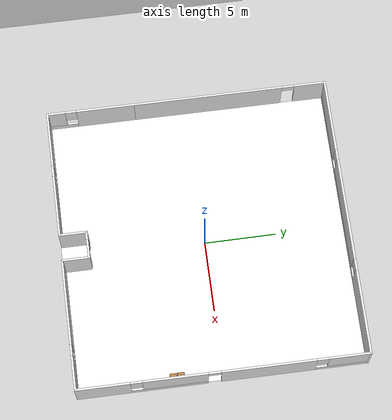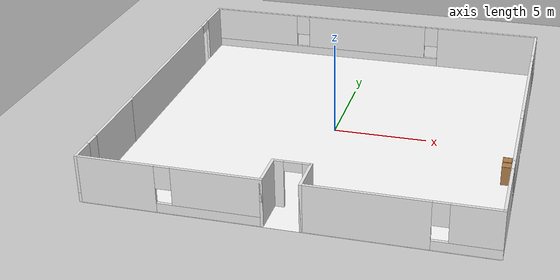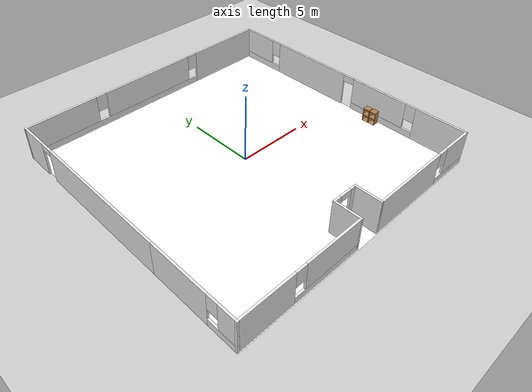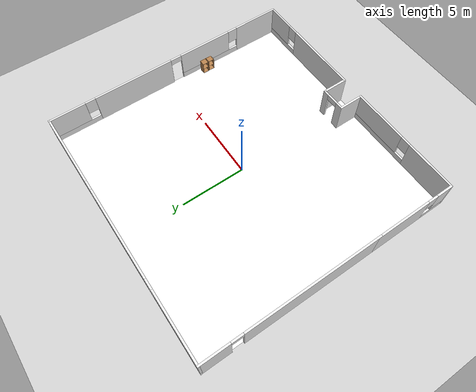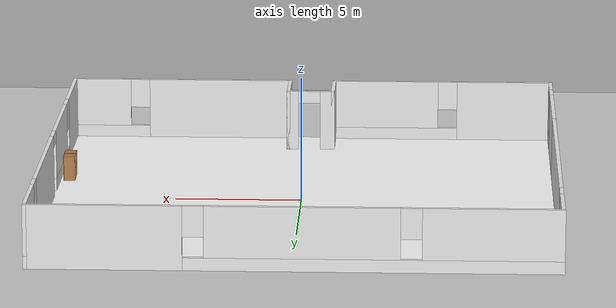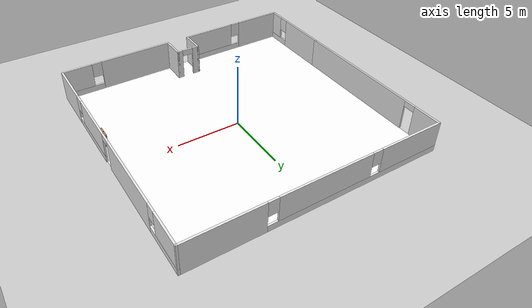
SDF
<sdf version="1.7">
 <world name="default">
  <light name="sun" type="directional">
   <pose>0 0 10 0 -0 0</pose>
   <diffuse>0.8 0.8 0.8 1</diffuse>
   <specular>0.2 0.2 0.2 1</specular>
   <attenuation>
    <range>1000</range>
    <constant>0.9</constant>
    <linear>0.01</linear>
    <quadratic>0.001</quadratic>
   </attenuation>
   <direction>-0.5 0.1 -0.9</direction>
   <spot><inner_angle>0</inner_angle><outer_angle>0</outer_angle><falloff>0</falloff></spot>
  </light>
  <model name="ground_plane">
   <static>1</static>
   <link name="link">
    <collision name="collision">
     <geometry><plane><normal>0 0 1</normal><size>100 100</size></plane></geometry>
     <surface><friction><ode><mu>100</mu><mu2>50</mu2></ode></friction></surface>
    </collision>
    <visual name="visual">
     <cast_shadows>0</cast_shadows>
     <geometry><plane><normal>0 0 1</normal><size>100 100</size></plane></geometry>
     <material>
      <script><uri>file://media/materials/scripts/gazebo.material</uri><name>Gazebo/Grey</name></script>
     </material>
    </visual>
   </link>
  </model>
  <gravity>0 0 -9.8</gravity>
  <magnetic_field>6e-06 2.3e-05 -4.2e-05</magnetic_field>
  <atmosphere type="adiabatic"/>
  <physics type="ode">
   <max_step_size>0.001</max_step_size>
   <real_time_factor>1</real_time_factor>
   <real_time_update_rate>1000</real_time_update_rate>
  </physics>
  <scene><ambient>0.4 0.4 0.4 1</ambient><background>0.7 0.7 0.7 1</background><shadows>1</shadows></scene>
  <spherical_coordinates>
   <surface_model>EARTH_WGS84</surface_model>
   <latitude_deg>0</latitude_deg>
   <longitude_deg>0</longitude_deg>
   <elevation>0</elevation>
   <heading_deg>0</heading_deg>
  </spherical_coordinates>
  <model name="office_env_w_complete_new">
   <link name="Wall_10">
    <pose>-5.46873 -9.925 0 0 -0 0</pose>
    <visual name="Wall_10_Visual_0">
     <pose>-2.62812 0 1.25 0 -0 0</pose>
     <geometry><box><size>3.99376 0.15 2.5</size></box></geometry>
     <material>
      <script>
       <uri>model://office_env_w/materials/scripts</uri>
       <uri>model://office_env_w/materials/textures</uri>
       <name>wall_white</name>
      </script>
      <shader type="pixel"/>
     </material>
     <meta><layer>0</layer></meta>
    </visual>
    <visual name="Wall_10_Visual_1">
     <pose>1.99688 0 0.25 0 -0 0</pose>
     <geometry><box><size>5.25624 0.15 0.5</size></box></geometry>
     <material>
      <script>
       <uri>model://office_env_w/materials/scripts</uri>
       <uri>model://office_env_w/materials/textures</uri>
       <name>wall_white</name>
      </script>
      <shader type="pixel"/>
     </material>
     <meta><layer>0</layer></meta>
    </visual>
    <visual name="Wall_10_Visual_2">
     <pose>2.39688 0 1.5 0 -0 0</pose>
     <geometry><box><size>4.45624 0.15 2</size></box></geometry>
     <material>
      <script>
       <uri>model://office_env_w/materials/scripts</uri>
       <uri>model://office_env_w/materials/textures</uri>
       <name>wall_white</name>
      </script>
      <shader type="pixel"/>
     </material>
     <meta><layer>0</layer></meta>
    </visual>
    <visual name="Wall_10_Visual_3">
     <pose>-0.231239 0 1.9 0 -0 0</pose>
     <geometry><box><size>0.8 0.15 1.2</size></box></geometry>
     <material>
      <script>
       <uri>model://office_env_w/materials/scripts</uri>
       <uri>model://office_env_w/materials/textures</uri>
       <name>wall_white</name>
      </script>
      <shader type="pixel"/>
     </material>
     <meta><layer>0</layer></meta>
    </visual>
    <collision name="Wall_10_Collision_0">
     <pose>-2.62812 0 1.25 0 -0 0</pose>
     <geometry><box><size>3.99376 0.15 2.5</size></box></geometry>
     <surface>
      <friction>
       <ode><mu>1</mu><mu2>1</mu2><fdir1>0 0 0</fdir1><slip1>0</slip1><slip2>0</slip2></ode>
       <torsional>
        <coefficient>1</coefficient>
        <patch_radius>0</patch_radius>
        <surface_radius>0</surface_radius>
        <use_patch_radius>1</use_patch_radius>
        <ode><slip>0</slip></ode>
       </torsional>
      </friction>
      <bounce><restitution_coefficient>0</restitution_coefficient><threshold>1e+06</threshold></bounce>
      <contact>
       <collide_without_contact>0</collide_without_contact>
       <collide_without_contact_bitmask>1</collide_without_contact_bitmask>
       <collide_bitmask>1</collide_bitmask>
       <ode>
        <soft_cfm>0</soft_cfm>
        <soft_erp>0.2</soft_erp>
        <kp>1e+13</kp>
        <kd>1</kd>
        <max_vel>0.01</max_vel>
        <min_depth>0</min_depth>
       </ode>
       <bullet>
        <split_impulse>1</split_impulse>
        <split_impulse_penetration_threshold>-0.01</split_impulse_penetration_threshold>
        <soft_cfm>0</soft_cfm>
        <soft_erp>0.2</soft_erp>
        <kp>1e+13</kp>
        <kd>1</kd>
       </bullet>
      </contact>
     </surface>
    </collision>
    <collision name="Wall_10_Collision_2">
     <pose>2.39688 0 1.5 0 -0 0</pose>
     <geometry><box><size>4.45624 0.15 2</size></box></geometry>
     <surface>
      <friction>
       <ode><mu>1</mu><mu2>1</mu2><fdir1>0 0 0</fdir1><slip1>0</slip1><slip2>0</slip2></ode>
       <torsional>
        <coefficient>1</coefficient>
        <patch_radius>0</patch_radius>
        <surface_radius>0</surface_radius>
        <use_patch_radius>1</use_patch_radius>
        <ode><slip>0</slip></ode>
       </torsional>
      </friction>
      <bounce><restitution_coefficient>0</restitution_coefficient><threshold>1e+06</threshold></bounce>
      <contact>
       <collide_without_contact>0</collide_without_contact>
       <collide_without_contact_bitmask>1</collide_without_contact_bitmask>
       <collide_bitmask>1</collide_bitmask>
       <ode>
        <soft_cfm>0</soft_cfm>
        <soft_erp>0.2</soft_erp>
        <kp>1e+13</kp>
        <kd>1</kd>
        <max_vel>0.01</max_vel>
        <min_depth>0</min_depth>
       </ode>
       <bullet>
        <split_impulse>1</split_impulse>
        <split_impulse_penetration_threshold>-0.01</split_impulse_penetration_threshold>
        <soft_cfm>0</soft_cfm>
        <soft_erp>0.2</soft_erp>
        <kp>1e+13</kp>
        <kd>1</kd>
       </bullet>
      </contact>
     </surface>
    </collision>
    <collision name="Wall_10_Collision_1">
     <pose>1.99688 0 0.25 0 -0 0</pose>
     <geometry><box><size>5.25624 0.15 0.5</size></box></geometry>
     <surface>
      <friction>
       <ode><mu>1</mu><mu2>1</mu2><fdir1>0 0 0</fdir1><slip1>0</slip1><slip2>0</slip2></ode>
       <torsional>
        <coefficient>1</coefficient>
        <patch_radius>0</patch_radius>
        <surface_radius>0</surface_radius>
        <use_patch_radius>1</use_patch_radius>
        <ode><slip>0</slip></ode>
       </torsional>
      </friction>
      <bounce><restitution_coefficient>0</restitution_coefficient><threshold>1e+06</threshold></bounce>
      <contact>
       <collide_without_contact>0</collide_without_contact>
       <collide_without_contact_bitmask>1</collide_without_contact_bitmask>
       <collide_bitmask>1</collide_bitmask>
       <ode>
        <soft_cfm>0</soft_cfm>
        <soft_erp>0.2</soft_erp>
        <kp>1e+13</kp>
        <kd>1</kd>
        <max_vel>0.01</max_vel>
        <min_depth>0</min_depth>
       </ode>
       <bullet>
        <split_impulse>1</split_impulse>
        <split_impulse_penetration_threshold>-0.01</split_impulse_penetration_threshold>
        <soft_cfm>0</soft_cfm>
        <soft_erp>0.2</soft_erp>
        <kp>1e+13</kp>
        <kd>1</kd>
       </bullet>
      </contact>
     </surface>
    </collision>
    <collision name="Wall_10_Collision_3">
     <pose>-0.231239 0 1.9 0 -0 0</pose>
     <geometry><box><size>0.8 0.15 1.2</size></box></geometry>
     <surface>
      <friction>
       <ode><mu>1</mu><mu2>1</mu2><fdir1>0 0 0</fdir1><slip1>0</slip1><slip2>0</slip2></ode>
       <torsional>
        <coefficient>1</coefficient>
        <patch_radius>0</patch_radius>
        <surface_radius>0</surface_radius>
        <use_patch_radius>1</use_patch_radius>
        <ode><slip>0</slip></ode>
       </torsional>
      </friction>
      <bounce><restitution_coefficient>0</restitution_coefficient><threshold>1e+06</threshold></bounce>
      <contact>
       <collide_without_contact>0</collide_without_contact>
       <collide_without_contact_bitmask>1</collide_without_contact_bitmask>
       <collide_bitmask>1</collide_bitmask>
       <ode>
        <soft_cfm>0</soft_cfm>
        <soft_erp>0.2</soft_erp>
        <kp>1e+13</kp>
        <kd>1</kd>
        <max_vel>0.01</max_vel>
        <min_depth>0</min_depth>
       </ode>
       <bullet>
        <split_impulse>1</split_impulse>
        <split_impulse_penetration_threshold>-0.01</split_impulse_penetration_threshold>
        <soft_cfm>0</soft_cfm>
        <soft_erp>0.2</soft_erp>
        <kp>1e+13</kp>
        <kd>1</kd>
       </bullet>
      </contact>
     </surface>
    </collision>
   </link>
   <link name="Wall_11">
    <pose>-0.918728 -9 0 0 -0 1.5708</pose>
    <visual name="Wall_11_Visual">
     <pose>0 0 1.25 0 -0 0</pose>
     <geometry><box><size>2 0.15 2.5</size></box></geometry>
     <material>
      <script>
       <uri>model://office_env_w/materials/scripts</uri>
       <uri>model://office_env_w/materials/textures</uri>
       <name>wall_white</name>
      </script>
      <shader type="pixel"/>
     </material>
     <meta><layer>0</layer></meta>
    </visual>
    <collision name="Wall_11_Collision">
     <pose>0 0 1.25 0 -0 0</pose>
     <geometry><box><size>2 0.15 2.5</size></box></geometry>
     <surface>
      <friction>
       <ode><mu>1</mu><mu2>1</mu2><fdir1>0 0 0</fdir1><slip1>0</slip1><slip2>0</slip2></ode>
       <torsional>
        <coefficient>1</coefficient>
        <patch_radius>0</patch_radius>
        <surface_radius>0</surface_radius>
        <use_patch_radius>1</use_patch_radius>
        <ode><slip>0</slip></ode>
       </torsional>
      </friction>
      <bounce><restitution_coefficient>0</restitution_coefficient><threshold>1e+06</threshold></bounce>
      <contact>
       <collide_without_contact>0</collide_without_contact>
       <collide_without_contact_bitmask>1</collide_without_contact_bitmask>
       <collide_bitmask>1</collide_bitmask>
       <ode>
        <soft_cfm>0</soft_cfm>
        <soft_erp>0.2</soft_erp>
        <kp>1e+13</kp>
        <kd>1</kd>
        <max_vel>0.01</max_vel>
        <min_depth>0</min_depth>
       </ode>
       <bullet>
        <split_impulse>1</split_impulse>
        <split_impulse_penetration_threshold>-0.01</split_impulse_penetration_threshold>
        <soft_cfm>0</soft_cfm>
        <soft_erp>0.2</soft_erp>
        <kp>1e+13</kp>
        <kd>1</kd>
       </bullet>
      </contact>
     </surface>
    </collision>
   </link>
   <link name="Wall_12">
    <pose>0.006272 -8.075 0 0 -0 0</pose>
    <visual name="Wall_12_Visual_1">
     <pose>0.754347 0 1.25 0 -0 0</pose>
     <geometry><box><size>0.491306 0.15 2.5</size></box></geometry>
     <material>
      <script>
       <uri>model://office_env_w/materials/scripts</uri>
       <uri>model://office_env_w/materials/textures</uri>
       <name>wall_white</name>
      </script>
      <shader type="pixel"/>
     </material>
     <meta><layer>0</layer></meta>
    </visual>
    <visual name="Wall_12_Visual_0">
     <pose>-0.695653 0 1.25 0 -0 0</pose>
     <geometry><box><size>0.608694 0.15 2.5</size></box></geometry>
     <material>
      <script>
       <uri>model://office_env_w/materials/scripts</uri>
       <uri>model://office_env_w/materials/textures</uri>
       <name>wall_white</name>
      </script>
      <shader type="pixel"/>
     </material>
     <meta><layer>0</layer></meta>
    </visual>
    <visual name="Wall_12_Visual_2">
     <pose>0.058694 0 2.25 0 -0 0</pose>
     <geometry><box><size>0.9 0.15 0.5</size></box></geometry>
     <material>
      <script>
       <uri>model://office_env_w/materials/scripts</uri>
       <uri>model://office_env_w/materials/textures</uri>
       <name>wall_white</name>
      </script>
      <shader type="pixel"/>
     </material>
     <meta><layer>0</layer></meta>
    </visual>
    <collision name="Wall_12_Collision_0">
     <pose>-0.695653 0 1.25 0 -0 0</pose>
     <geometry><box><size>0.608694 0.15 2.5</size></box></geometry>
     <surface>
      <friction>
       <ode><mu>1</mu><mu2>1</mu2><fdir1>0 0 0</fdir1><slip1>0</slip1><slip2>0</slip2></ode>
       <torsional>
        <coefficient>1</coefficient>
        <patch_radius>0</patch_radius>
        <surface_radius>0</surface_radius>
        <use_patch_radius>1</use_patch_radius>
        <ode><slip>0</slip></ode>
       </torsional>
      </friction>
      <bounce><restitution_coefficient>0</restitution_coefficient><threshold>1e+06</threshold></bounce>
      <contact>
       <collide_without_contact>0</collide_without_contact>
       <collide_without_contact_bitmask>1</collide_without_contact_bitmask>
       <collide_bitmask>1</collide_bitmask>
       <ode>
        <soft_cfm>0</soft_cfm>
        <soft_erp>0.2</soft_erp>
        <kp>1e+13</kp>
        <kd>1</kd>
        <max_vel>0.01</max_vel>
        <min_depth>0</min_depth>
       </ode>
       <bullet>
        <split_impulse>1</split_impulse>
        <split_impulse_penetration_threshold>-0.01</split_impulse_penetration_threshold>
        <soft_cfm>0</soft_cfm>
        <soft_erp>0.2</soft_erp>
        <kp>1e+13</kp>
        <kd>1</kd>
       </bullet>
      </contact>
     </surface>
    </collision>
    <collision name="Wall_12_Collision_1">
     <pose>0.754347 0 1.25 0 -0 0</pose>
     <geometry><box><size>0.491306 0.15 2.5</size></box></geometry>
     <surface>
      <friction>
       <ode><mu>1</mu><mu2>1</mu2><fdir1>0 0 0</fdir1><slip1>0</slip1><slip2>0</slip2></ode>
       <torsional>
        <coefficient>1</coefficient>
        <patch_radius>0</patch_radius>
        <surface_radius>0</surface_radius>
        <use_patch_radius>1</use_patch_radius>
        <ode><slip>0</slip></ode>
       </torsional>
      </friction>
      <bounce><restitution_coefficient>0</restitution_coefficient><threshold>1e+06</threshold></bounce>
      <contact>
       <collide_without_contact>0</collide_without_contact>
       <collide_without_contact_bitmask>1</collide_without_contact_bitmask>
       <collide_bitmask>1</collide_bitmask>
       <ode>
        <soft_cfm>0</soft_cfm>
        <soft_erp>0.2</soft_erp>
        <kp>1e+13</kp>
        <kd>1</kd>
        <max_vel>0.01</max_vel>
        <min_depth>0</min_depth>
       </ode>
       <bullet>
        <split_impulse>1</split_impulse>
        <split_impulse_penetration_threshold>-0.01</split_impulse_penetration_threshold>
        <soft_cfm>0</soft_cfm>
        <soft_erp>0.2</soft_erp>
        <kp>1e+13</kp>
        <kd>1</kd>
       </bullet>
      </contact>
     </surface>
    </collision>
    <collision name="Wall_12_Collision_2">
     <pose>0.058694 0 2.25 0 -0 0</pose>
     <geometry><box><size>0.9 0.15 0.5</size></box></geometry>
     <surface>
      <friction>
       <ode><mu>1</mu><mu2>1</mu2><fdir1>0 0 0</fdir1><slip1>0</slip1><slip2>0</slip2></ode>
       <torsional>
        <coefficient>1</coefficient>
        <patch_radius>0</patch_radius>
        <surface_radius>0</surface_radius>
        <use_patch_radius>1</use_patch_radius>
        <ode><slip>0</slip></ode>
       </torsional>
      </friction>
      <bounce><restitution_coefficient>0</restitution_coefficient><threshold>1e+06</threshold></bounce>
      <contact>
       <collide_without_contact>0</collide_without_contact>
       <collide_without_contact_bitmask>1</collide_without_contact_bitmask>
       <collide_bitmask>1</collide_bitmask>
       <ode>
        <soft_cfm>0</soft_cfm>
        <soft_erp>0.2</soft_erp>
        <kp>1e+13</kp>
        <kd>1</kd>
        <max_vel>0.01</max_vel>
        <min_depth>0</min_depth>
       </ode>
       <bullet>
        <split_impulse>1</split_impulse>
        <split_impulse_penetration_threshold>-0.01</split_impulse_penetration_threshold>
        <soft_cfm>0</soft_cfm>
        <soft_erp>0.2</soft_erp>
        <kp>1e+13</kp>
        <kd>1</kd>
       </bullet>
      </contact>
     </surface>
    </collision>
   </link>
   <link name="Wall_15">
    <pose>0.931272 -9 0 0 0 -1.5708</pose>
    <visual name="Wall_15_Visual">
     <pose>0 0 1.25 0 -0 0</pose>
     <geometry><box><size>2 0.15 2.5</size></box></geometry>
     <material>
      <script>
       <uri>model://office_env_w/materials/scripts</uri>
       <uri>model://office_env_w/materials/textures</uri>
       <name>wall_white</name>
      </script>
      <shader type="pixel"/>
     </material>
     <meta><layer>0</layer></meta>
    </visual>
    <collision name="Wall_15_Collision">
     <pose>0 0 1.25 0 -0 0</pose>
     <geometry><box><size>2 0.15 2.5</size></box></geometry>
     <surface>
      <friction>
       <ode><mu>1</mu><mu2>1</mu2><fdir1>0 0 0</fdir1><slip1>0</slip1><slip2>0</slip2></ode>
       <torsional>
        <coefficient>1</coefficient>
        <patch_radius>0</patch_radius>
        <surface_radius>0</surface_radius>
        <use_patch_radius>1</use_patch_radius>
        <ode><slip>0</slip></ode>
       </torsional>
      </friction>
      <bounce><restitution_coefficient>0</restitution_coefficient><threshold>1e+06</threshold></bounce>
      <contact>
       <collide_without_contact>0</collide_without_contact>
       <collide_without_contact_bitmask>1</collide_without_contact_bitmask>
       <collide_bitmask>1</collide_bitmask>
       <ode>
        <soft_cfm>0</soft_cfm>
        <soft_erp>0.2</soft_erp>
        <kp>1e+13</kp>
        <kd>1</kd>
        <max_vel>0.01</max_vel>
        <min_depth>0</min_depth>
       </ode>
       <bullet>
        <split_impulse>1</split_impulse>
        <split_impulse_penetration_threshold>-0.01</split_impulse_penetration_threshold>
        <soft_cfm>0</soft_cfm>
        <soft_erp>0.2</soft_erp>
        <kp>1e+13</kp>
        <kd>1</kd>
       </bullet>
      </contact>
     </surface>
    </collision>
   </link>
   <link name="Wall_16">
    <pose>5.48127 -9.925 0 0 -0 0</pose>
    <visual name="Wall_16_Visual_0">
     <pose>-1.61303 0 1.25 0 -0 0</pose>
     <geometry><box><size>6.02393 0.15 2.5</size></box></geometry>
     <material>
      <script>
       <uri>model://office_env_w/materials/scripts</uri>
       <uri>model://office_env_w/materials/textures</uri>
       <name>wall_white</name>
      </script>
      <shader type="pixel"/>
     </material>
     <meta><layer>0</layer></meta>
    </visual>
    <visual name="Wall_16_Visual_1">
     <pose>3.01197 0 0.25 0 -0 0</pose>
     <geometry><box><size>3.22607 0.15 0.5</size></box></geometry>
     <material>
      <script>
       <uri>model://office_env_w/materials/scripts</uri>
       <uri>model://office_env_w/materials/textures</uri>
       <name>wall_white</name>
      </script>
      <shader type="pixel"/>
     </material>
     <meta><layer>0</layer></meta>
    </visual>
    <visual name="Wall_16_Visual_2">
     <pose>3.41197 0 1.5 0 -0 0</pose>
     <geometry><box><size>2.42607 0.15 2</size></box></geometry>
     <material>
      <script>
       <uri>model://office_env_w/materials/scripts</uri>
       <uri>model://office_env_w/materials/textures</uri>
       <name>wall_white</name>
      </script>
      <shader type="pixel"/>
     </material>
     <meta><layer>0</layer></meta>
    </visual>
    <visual name="Wall_16_Visual_3">
     <pose>1.79893 0 1.9 0 -0 0</pose>
     <geometry><box><size>0.8 0.15 1.2</size></box></geometry>
     <material>
      <script>
       <uri>model://office_env_w/materials/scripts</uri>
       <uri>model://office_env_w/materials/textures</uri>
       <name>wall_white</name>
      </script>
      <shader type="pixel"/>
     </material>
     <meta><layer>0</layer></meta>
    </visual>
    <collision name="Wall_16_Collision_0">
     <pose>-1.61303 0 1.25 0 -0 0</pose>
     <geometry><box><size>6.02393 0.15 2.5</size></box></geometry>
     <surface>
      <friction>
       <ode><mu>1</mu><mu2>1</mu2><fdir1>0 0 0</fdir1><slip1>0</slip1><slip2>0</slip2></ode>
       <torsional>
        <coefficient>1</coefficient>
        <patch_radius>0</patch_radius>
        <surface_radius>0</surface_radius>
        <use_patch_radius>1</use_patch_radius>
        <ode><slip>0</slip></ode>
       </torsional>
      </friction>
      <bounce><restitution_coefficient>0</restitution_coefficient><threshold>1e+06</threshold></bounce>
      <contact>
       <collide_without_contact>0</collide_without_contact>
       <collide_without_contact_bitmask>1</collide_without_contact_bitmask>
       <collide_bitmask>1</collide_bitmask>
       <ode>
        <soft_cfm>0</soft_cfm>
        <soft_erp>0.2</soft_erp>
        <kp>1e+13</kp>
        <kd>1</kd>
        <max_vel>0.01</max_vel>
        <min_depth>0</min_depth>
       </ode>
       <bullet>
        <split_impulse>1</split_impulse>
        <split_impulse_penetration_threshold>-0.01</split_impulse_penetration_threshold>
        <soft_cfm>0</soft_cfm>
        <soft_erp>0.2</soft_erp>
        <kp>1e+13</kp>
        <kd>1</kd>
       </bullet>
      </contact>
     </surface>
    </collision>
    <collision name="Wall_16_Collision_1">
     <pose>3.01197 0 0.25 0 -0 0</pose>
     <geometry><box><size>3.22607 0.15 0.5</size></box></geometry>
     <surface>
      <friction>
       <ode><mu>1</mu><mu2>1</mu2><fdir1>0 0 0</fdir1><slip1>0</slip1><slip2>0</slip2></ode>
       <torsional>
        <coefficient>1</coefficient>
        <patch_radius>0</patch_radius>
        <surface_radius>0</surface_radius>
        <use_patch_radius>1</use_patch_radius>
        <ode><slip>0</slip></ode>
       </torsional>
      </friction>
      <bounce><restitution_coefficient>0</restitution_coefficient><threshold>1e+06</threshold></bounce>
      <contact>
       <collide_without_contact>0</collide_without_contact>
       <collide_without_contact_bitmask>1</collide_without_contact_bitmask>
       <collide_bitmask>1</collide_bitmask>
       <ode>
        <soft_cfm>0</soft_cfm>
        <soft_erp>0.2</soft_erp>
        <kp>1e+13</kp>
        <kd>1</kd>
        <max_vel>0.01</max_vel>
        <min_depth>0</min_depth>
       </ode>
       <bullet>
        <split_impulse>1</split_impulse>
        <split_impulse_penetration_threshold>-0.01</split_impulse_penetration_threshold>
        <soft_cfm>0</soft_cfm>
        <soft_erp>0.2</soft_erp>
        <kp>1e+13</kp>
        <kd>1</kd>
       </bullet>
      </contact>
     </surface>
    </collision>
    <collision name="Wall_16_Collision_2">
     <pose>3.41197 0 1.5 0 -0 0</pose>
     <geometry><box><size>2.42607 0.15 2</size></box></geometry>
     <surface>
      <friction>
       <ode><mu>1</mu><mu2>1</mu2><fdir1>0 0 0</fdir1><slip1>0</slip1><slip2>0</slip2></ode>
       <torsional>
        <coefficient>1</coefficient>
        <patch_radius>0</patch_radius>
        <surface_radius>0</surface_radius>
        <use_patch_radius>1</use_patch_radius>
        <ode><slip>0</slip></ode>
       </torsional>
      </friction>
      <bounce><restitution_coefficient>0</restitution_coefficient><threshold>1e+06</threshold></bounce>
      <contact>
       <collide_without_contact>0</collide_without_contact>
       <collide_without_contact_bitmask>1</collide_without_contact_bitmask>
       <collide_bitmask>1</collide_bitmask>
       <ode>
        <soft_cfm>0</soft_cfm>
        <soft_erp>0.2</soft_erp>
        <kp>1e+13</kp>
        <kd>1</kd>
        <max_vel>0.01</max_vel>
        <min_depth>0</min_depth>
       </ode>
       <bullet>
        <split_impulse>1</split_impulse>
        <split_impulse_penetration_threshold>-0.01</split_impulse_penetration_threshold>
        <soft_cfm>0</soft_cfm>
        <soft_erp>0.2</soft_erp>
        <kp>1e+13</kp>
        <kd>1</kd>
       </bullet>
      </contact>
     </surface>
    </collision>
    <collision name="Wall_16_Collision_3">
     <pose>1.79893 0 1.9 0 -0 0</pose>
     <geometry><box><size>0.8 0.15 1.2</size></box></geometry>
     <surface>
      <friction>
       <ode><mu>1</mu><mu2>1</mu2><fdir1>0 0 0</fdir1><slip1>0</slip1><slip2>0</slip2></ode>
       <torsional>
        <coefficient>1</coefficient>
        <patch_radius>0</patch_radius>
        <surface_radius>0</surface_radius>
        <use_patch_radius>1</use_patch_radius>
        <ode><slip>0</slip></ode>
       </torsional>
      </friction>
      <bounce><restitution_coefficient>0</restitution_coefficient><threshold>1e+06</threshold></bounce>
      <contact>
       <collide_without_contact>0</collide_without_contact>
       <collide_without_contact_bitmask>1</collide_without_contact_bitmask>
       <collide_bitmask>1</collide_bitmask>
       <ode>
        <soft_cfm>0</soft_cfm>
        <soft_erp>0.2</soft_erp>
        <kp>1e+13</kp>
        <kd>1</kd>
        <max_vel>0.01</max_vel>
        <min_depth>0</min_depth>
       </ode>
       <bullet>
        <split_impulse>1</split_impulse>
        <split_impulse_penetration_threshold>-0.01</split_impulse_penetration_threshold>
        <soft_cfm>0</soft_cfm>
        <soft_erp>0.2</soft_erp>
        <kp>1e+13</kp>
        <kd>1</kd>
       </bullet>
      </contact>
     </surface>
    </collision>
   </link>
   <link name="Wall_17">
    <pose>10.0313 0 0 0 -0 1.5708</pose>
    <visual name="Wall_17_Visual_0">
     <pose>-8.12184 0 1.25 0 -0 0</pose>
     <geometry><box><size>3.75631 0.15 2.5</size></box></geometry>
     <material>
      <script>
       <uri>model://office_env_w/materials/scripts</uri>
       <uri>model://office_env_w/materials/textures</uri>
       <name>wall_white</name>
      </script>
      <shader type="pixel"/>
     </material>
     <meta><layer>0</layer></meta>
    </visual>
    <visual name="Wall_17_Visual_1">
     <pose>3.09096 0 1.25 0 -0 0</pose>
     <geometry><box><size>6.45362 0.15 2.5</size></box></geometry>
     <material>
      <script>
       <uri>model://office_env_w/materials/scripts</uri>
       <uri>model://office_env_w/materials/textures</uri>
       <name>wall_white</name>
      </script>
      <shader type="pixel"/>
     </material>
     <meta><layer>0</layer></meta>
    </visual>
    <visual name="Wall_17_Visual_2">
     <pose>-3.63977 0 0.25 0 -0 0</pose>
     <geometry><box><size>5.20784 0.15 0.5</size></box></geometry>
     <material>
      <script>
       <uri>model://office_env_w/materials/scripts</uri>
       <uri>model://office_env_w/materials/textures</uri>
       <name>wall_white</name>
      </script>
      <shader type="pixel"/>
     </material>
     <meta><layer>0</layer></meta>
    </visual>
    <visual name="Wall_17_Visual_3">
     <pose>8.15888 0 0.25 0 -0 0</pose>
     <geometry><box><size>3.68223 0.15 0.5</size></box></geometry>
     <material>
      <script>
       <uri>model://office_env_w/materials/scripts</uri>
       <uri>model://office_env_w/materials/textures</uri>
       <name>wall_white</name>
      </script>
      <shader type="pixel"/>
     </material>
     <meta><layer>0</layer></meta>
    </visual>
    <visual name="Wall_17_Visual_4">
     <pose>-3.23977 0 1.5 0 -0 0</pose>
     <geometry><box><size>4.40784 0.15 2</size></box></geometry>
     <material>
      <script>
       <uri>model://office_env_w/materials/scripts</uri>
       <uri>model://office_env_w/materials/textures</uri>
       <name>wall_white</name>
      </script>
      <shader type="pixel"/>
     </material>
     <meta><layer>0</layer></meta>
    </visual>
    <visual name="Wall_17_Visual_5">
     <pose>-3.23977 0 1.5 0 -0 0</pose>
     <geometry><box><size>4.40784 0.15 2</size></box></geometry>
     <material>
      <script>
       <uri>model://office_env_w/materials/scripts</uri>
       <uri>model://office_env_w/materials/textures</uri>
       <name>wall_white</name>
      </script>
      <shader type="pixel"/>
     </material>
     <meta><layer>0</layer></meta>
    </visual>
    <visual name="Wall_17_Visual_6">
     <pose>8.55889 0 1.5 0 -0 0</pose>
     <geometry><box><size>2.88223 0.15 2</size></box></geometry>
     <material>
      <script>
       <uri>model://office_env_w/materials/scripts</uri>
       <uri>model://office_env_w/materials/textures</uri>
       <name>wall_white</name>
      </script>
      <shader type="pixel"/>
     </material>
     <meta><layer>0</layer></meta>
    </visual>
    <visual name="Wall_17_Visual_7">
     <pose>-5.84369 0 1.9 0 -0 0</pose>
     <geometry><box><size>0.8 0.15 1.2</size></box></geometry>
     <material>
      <script>
       <uri>model://office_env_w/materials/scripts</uri>
       <uri>model://office_env_w/materials/textures</uri>
       <name>wall_white</name>
      </script>
      <shader type="pixel"/>
     </material>
     <meta><layer>0</layer></meta>
    </visual>
    <visual name="Wall_17_Visual_8">
     <pose>6.71777 0 1.9 0 -0 0</pose>
     <geometry><box><size>0.8 0.15 1.2</size></box></geometry>
     <material>
      <script>
       <uri>model://office_env_w/materials/scripts</uri>
       <uri>model://office_env_w/materials/textures</uri>
       <name>wall_white</name>
      </script>
      <shader type="pixel"/>
     </material>
     <meta><layer>0</layer></meta>
    </visual>
    <visual name="Wall_17_Visual_9">
     <pose>-0.585848 0 2.25 0 -0 0</pose>
     <geometry><box><size>0.9 0.15 0.5</size></box></geometry>
     <material>
      <script>
       <uri>model://office_env_w/materials/scripts</uri>
       <uri>model://office_env_w/materials/textures</uri>
       <name>wall_white</name>
      </script>
      <shader type="pixel"/>
     </material>
     <meta><layer>0</layer></meta>
    </visual>
    <visual name="Wall_17_Visual_10">
     <pose>-0.585848 0 2.25 0 -0 0</pose>
     <geometry><box><size>0.9 0.15 0.5</size></box></geometry>
     <material>
      <script>
       <uri>model://office_env_w/materials/scripts</uri>
       <uri>model://office_env_w/materials/textures</uri>
       <name>wall_white</name>
      </script>
      <shader type="pixel"/>
     </material>
     <meta><layer>0</layer></meta>
    </visual>
    <collision name="Wall_17_Collision_0">
     <pose>-8.12184 0 1.25 0 -0 0</pose>
     <geometry><box><size>3.75631 0.15 2.5</size></box></geometry>
     <surface>
      <friction>
       <ode><mu>1</mu><mu2>1</mu2><fdir1>0 0 0</fdir1><slip1>0</slip1><slip2>0</slip2></ode>
       <torsional>
        <coefficient>1</coefficient>
        <patch_radius>0</patch_radius>
        <surface_radius>0</surface_radius>
        <use_patch_radius>1</use_patch_radius>
        <ode><slip>0</slip></ode>
       </torsional>
      </friction>
      <bounce><restitution_coefficient>0</restitution_coefficient><threshold>1e+06</threshold></bounce>
      <contact>
       <collide_without_contact>0</collide_without_contact>
       <collide_without_contact_bitmask>1</collide_without_contact_bitmask>
       <collide_bitmask>1</collide_bitmask>
       <ode>
        <soft_cfm>0</soft_cfm>
        <soft_erp>0.2</soft_erp>
        <kp>1e+13</kp>
        <kd>1</kd>
        <max_vel>0.01</max_vel>
        <min_depth>0</min_depth>
       </ode>
       <bullet>
        <split_impulse>1</split_impulse>
        <split_impulse_penetration_threshold>-0.01</split_impulse_penetration_threshold>
        <soft_cfm>0</soft_cfm>
        <soft_erp>0.2</soft_erp>
        <kp>1e+13</kp>
        <kd>1</kd>
       </bullet>
      </contact>
     </surface>
    </collision>
    <collision name="Wall_17_Collision_1">
     <pose>3.09096 0 1.25 0 -0 0</pose>
     <geometry><box><size>6.45362 0.15 2.5</size></box></geometry>
     <surface>
      <friction>
       <ode><mu>1</mu><mu2>1</mu2><fdir1>0 0 0</fdir1><slip1>0</slip1><slip2>0</slip2></ode>
       <torsional>
        <coefficient>1</coefficient>
        <patch_radius>0</patch_radius>
        <surface_radius>0</surface_radius>
        <use_patch_radius>1</use_patch_radius>
        <ode><slip>0</slip></ode>
       </torsional>
      </friction>
      <bounce><restitution_coefficient>0</restitution_coefficient><threshold>1e+06</threshold></bounce>
      <contact>
       <collide_without_contact>0</collide_without_contact>
       <collide_without_contact_bitmask>1</collide_without_contact_bitmask>
       <collide_bitmask>1</collide_bitmask>
       <ode>
        <soft_cfm>0</soft_cfm>
        <soft_erp>0.2</soft_erp>
        <kp>1e+13</kp>
        <kd>1</kd>
        <max_vel>0.01</max_vel>
        <min_depth>0</min_depth>
       </ode>
       <bullet>
        <split_impulse>1</split_impulse>
        <split_impulse_penetration_threshold>-0.01</split_impulse_penetration_threshold>
        <soft_cfm>0</soft_cfm>
        <soft_erp>0.2</soft_erp>
        <kp>1e+13</kp>
        <kd>1</kd>
       </bullet>
      </contact>
     </surface>
    </collision>
    <collision name="Wall_17_Collision_2">
     <pose>-3.63977 0 0.25 0 -0 0</pose>
     <geometry><box><size>5.20784 0.15 0.5</size></box></geometry>
     <surface>
      <friction>
       <ode><mu>1</mu><mu2>1</mu2><fdir1>0 0 0</fdir1><slip1>0</slip1><slip2>0</slip2></ode>
       <torsional>
        <coefficient>1</coefficient>
        <patch_radius>0</patch_radius>
        <surface_radius>0</surface_radius>
        <use_patch_radius>1</use_patch_radius>
        <ode><slip>0</slip></ode>
       </torsional>
      </friction>
      <bounce><restitution_coefficient>0</restitution_coefficient><threshold>1e+06</threshold></bounce>
      <contact>
       <collide_without_contact>0</collide_without_contact>
       <collide_without_contact_bitmask>1</collide_without_contact_bitmask>
       <collide_bitmask>1</collide_bitmask>
       <ode>
        <soft_cfm>0</soft_cfm>
        <soft_erp>0.2</soft_erp>
        <kp>1e+13</kp>
        <kd>1</kd>
        <max_vel>0.01</max_vel>
        <min_depth>0</min_depth>
       </ode>
       <bullet>
        <split_impulse>1</split_impulse>
        <split_impulse_penetration_threshold>-0.01</split_impulse_penetration_threshold>
        <soft_cfm>0</soft_cfm>
        <soft_erp>0.2</soft_erp>
        <kp>1e+13</kp>
        <kd>1</kd>
       </bullet>
      </contact>
     </surface>
    </collision>
    <collision name="Wall_17_Collision_3">
     <pose>8.15888 0 0.25 0 -0 0</pose>
     <geometry><box><size>3.68223 0.15 0.5</size></box></geometry>
     <surface>
      <friction>
       <ode><mu>1</mu><mu2>1</mu2><fdir1>0 0 0</fdir1><slip1>0</slip1><slip2>0</slip2></ode>
       <torsional>
        <coefficient>1</coefficient>
        <patch_radius>0</patch_radius>
        <surface_radius>0</surface_radius>
        <use_patch_radius>1</use_patch_radius>
        <ode><slip>0</slip></ode>
       </torsional>
      </friction>
      <bounce><restitution_coefficient>0</restitution_coefficient><threshold>1e+06</threshold></bounce>
      <contact>
       <collide_without_contact>0</collide_without_contact>
       <collide_without_contact_bitmask>1</collide_without_contact_bitmask>
       <collide_bitmask>1</collide_bitmask>
       <ode>
        <soft_cfm>0</soft_cfm>
        <soft_erp>0.2</soft_erp>
        <kp>1e+13</kp>
        <kd>1</kd>
        <max_vel>0.01</max_vel>
        <min_depth>0</min_depth>
       </ode>
       <bullet>
        <split_impulse>1</split_impulse>
        <split_impulse_penetration_threshold>-0.01</split_impulse_penetration_threshold>
        <soft_cfm>0</soft_cfm>
        <soft_erp>0.2</soft_erp>
        <kp>1e+13</kp>
        <kd>1</kd>
       </bullet>
      </contact>
     </surface>
    </collision>
    <collision name="Wall_17_Collision_4">
     <pose>-3.23977 0 1.5 0 -0 0</pose>
     <geometry><box><size>4.40784 0.15 2</size></box></geometry>
     <surface>
      <friction>
       <ode><mu>1</mu><mu2>1</mu2><fdir1>0 0 0</fdir1><slip1>0</slip1><slip2>0</slip2></ode>
       <torsional>
        <coefficient>1</coefficient>
        <patch_radius>0</patch_radius>
        <surface_radius>0</surface_radius>
        <use_patch_radius>1</use_patch_radius>
        <ode><slip>0</slip></ode>
       </torsional>
      </friction>
      <bounce><restitution_coefficient>0</restitution_coefficient><threshold>1e+06</threshold></bounce>
      <contact>
       <collide_without_contact>0</collide_without_contact>
       <collide_without_contact_bitmask>1</collide_without_contact_bitmask>
       <collide_bitmask>1</collide_bitmask>
       <ode>
        <soft_cfm>0</soft_cfm>
        <soft_erp>0.2</soft_erp>
        <kp>1e+13</kp>
        <kd>1</kd>
        <max_vel>0.01</max_vel>
        <min_depth>0</min_depth>
       </ode>
       <bullet>
        <split_impulse>1</split_impulse>
        <split_impulse_penetration_threshold>-0.01</split_impulse_penetration_threshold>
        <soft_cfm>0</soft_cfm>
        <soft_erp>0.2</soft_erp>
        <kp>1e+13</kp>
        <kd>1</kd>
       </bullet>
      </contact>
     </surface>
    </collision>
    <collision name="Wall_17_Collision_5">
     <pose>-3.23977 0 1.5 0 -0 0</pose>
     <geometry><box><size>4.40784 0.15 2</size></box></geometry>
     <surface>
      <friction>
       <ode><mu>1</mu><mu2>1</mu2><fdir1>0 0 0</fdir1><slip1>0</slip1><slip2>0</slip2></ode>
       <torsional>
        <coefficient>1</coefficient>
        <patch_radius>0</patch_radius>
        <surface_radius>0</surface_radius>
        <use_patch_radius>1</use_patch_radius>
        <ode><slip>0</slip></ode>
       </torsional>
      </friction>
      <bounce><restitution_coefficient>0</restitution_coefficient><threshold>1e+06</threshold></bounce>
      <contact>
       <collide_without_contact>0</collide_without_contact>
       <collide_without_contact_bitmask>1</collide_without_contact_bitmask>
       <collide_bitmask>1</collide_bitmask>
       <ode>
        <soft_cfm>0</soft_cfm>
        <soft_erp>0.2</soft_erp>
        <kp>1e+13</kp>
        <kd>1</kd>
        <max_vel>0.01</max_vel>
        <min_depth>0</min_depth>
       </ode>
       <bullet>
        <split_impulse>1</split_impulse>
        <split_impulse_penetration_threshold>-0.01</split_impulse_penetration_threshold>
        <soft_cfm>0</soft_cfm>
        <soft_erp>0.2</soft_erp>
        <kp>1e+13</kp>
        <kd>1</kd>
       </bullet>
      </contact>
     </surface>
    </collision>
    <collision name="Wall_17_Collision_6">
     <pose>8.55889 0 1.5 0 -0 0</pose>
     <geometry><box><size>2.88223 0.15 2</size></box></geometry>
     <surface>
      <friction>
       <ode><mu>1</mu><mu2>1</mu2><fdir1>0 0 0</fdir1><slip1>0</slip1><slip2>0</slip2></ode>
       <torsional>
        <coefficient>1</coefficient>
        <patch_radius>0</patch_radius>
        <surface_radius>0</surface_radius>
        <use_patch_radius>1</use_patch_radius>
        <ode><slip>0</slip></ode>
       </torsional>
      </friction>
      <bounce><restitution_coefficient>0</restitution_coefficient><threshold>1e+06</threshold></bounce>
      <contact>
       <collide_without_contact>0</collide_without_contact>
       <collide_without_contact_bitmask>1</collide_without_contact_bitmask>
       <collide_bitmask>1</collide_bitmask>
       <ode>
        <soft_cfm>0</soft_cfm>
        <soft_erp>0.2</soft_erp>
        <kp>1e+13</kp>
        <kd>1</kd>
        <max_vel>0.01</max_vel>
        <min_depth>0</min_depth>
       </ode>
       <bullet>
        <split_impulse>1</split_impulse>
        <split_impulse_penetration_threshold>-0.01</split_impulse_penetration_threshold>
        <soft_cfm>0</soft_cfm>
        <soft_erp>0.2</soft_erp>
        <kp>1e+13</kp>
        <kd>1</kd>
       </bullet>
      </contact>
     </surface>
    </collision>
    <collision name="Wall_17_Collision_7">
     <pose>-5.84369 0 1.9 0 -0 0</pose>
     <geometry><box><size>0.8 0.15 1.2</size></box></geometry>
     <surface>
      <friction>
       <ode><mu>1</mu><mu2>1</mu2><fdir1>0 0 0</fdir1><slip1>0</slip1><slip2>0</slip2></ode>
       <torsional>
        <coefficient>1</coefficient>
        <patch_radius>0</patch_radius>
        <surface_radius>0</surface_radius>
        <use_patch_radius>1</use_patch_radius>
        <ode><slip>0</slip></ode>
       </torsional>
      </friction>
      <bounce><restitution_coefficient>0</restitution_coefficient><threshold>1e+06</threshold></bounce>
      <contact>
       <collide_without_contact>0</collide_without_contact>
       <collide_without_contact_bitmask>1</collide_without_contact_bitmask>
       <collide_bitmask>1</collide_bitmask>
       <ode>
        <soft_cfm>0</soft_cfm>
        <soft_erp>0.2</soft_erp>
        <kp>1e+13</kp>
        <kd>1</kd>
        <max_vel>0.01</max_vel>
        <min_depth>0</min_depth>
       </ode>
       <bullet>
        <split_impulse>1</split_impulse>
        <split_impulse_penetration_threshold>-0.01</split_impulse_penetration_threshold>
        <soft_cfm>0</soft_cfm>
        <soft_erp>0.2</soft_erp>
        <kp>1e+13</kp>
        <kd>1</kd>
       </bullet>
      </contact>
     </surface>
    </collision>
    <collision name="Wall_17_Collision_9">
     <pose>-0.585848 0 2.25 0 -0 0</pose>
     <geometry><box><size>0.9 0.15 0.5</size></box></geometry>
     <surface>
      <friction>
       <ode><mu>1</mu><mu2>1</mu2><fdir1>0 0 0</fdir1><slip1>0</slip1><slip2>0</slip2></ode>
       <torsional>
        <coefficient>1</coefficient>
        <patch_radius>0</patch_radius>
        <surface_radius>0</surface_radius>
        <use_patch_radius>1</use_patch_radius>
        <ode><slip>0</slip></ode>
       </torsional>
      </friction>
      <bounce><restitution_coefficient>0</restitution_coefficient><threshold>1e+06</threshold></bounce>
      <contact>
       <collide_without_contact>0</collide_without_contact>
       <collide_without_contact_bitmask>1</collide_without_contact_bitmask>
       <collide_bitmask>1</collide_bitmask>
       <ode>
        <soft_cfm>0</soft_cfm>
        <soft_erp>0.2</soft_erp>
        <kp>1e+13</kp>
        <kd>1</kd>
        <max_vel>0.01</max_vel>
        <min_depth>0</min_depth>
       </ode>
       <bullet>
        <split_impulse>1</split_impulse>
        <split_impulse_penetration_threshold>-0.01</split_impulse_penetration_threshold>
        <soft_cfm>0</soft_cfm>
        <soft_erp>0.2</soft_erp>
        <kp>1e+13</kp>
        <kd>1</kd>
       </bullet>
      </contact>
     </surface>
    </collision>
    <collision name="Wall_17_Collision_8">
     <pose>6.71777 0 1.9 0 -0 0</pose>
     <geometry><box><size>0.8 0.15 1.2</size></box></geometry>
     <surface>
      <friction>
       <ode><mu>1</mu><mu2>1</mu2><fdir1>0 0 0</fdir1><slip1>0</slip1><slip2>0</slip2></ode>
       <torsional>
        <coefficient>1</coefficient>
        <patch_radius>0</patch_radius>
        <surface_radius>0</surface_radius>
        <use_patch_radius>1</use_patch_radius>
        <ode><slip>0</slip></ode>
       </torsional>
      </friction>
      <bounce><restitution_coefficient>0</restitution_coefficient><threshold>1e+06</threshold></bounce>
      <contact>
       <collide_without_contact>0</collide_without_contact>
       <collide_without_contact_bitmask>1</collide_without_contact_bitmask>
       <collide_bitmask>1</collide_bitmask>
       <ode>
        <soft_cfm>0</soft_cfm>
        <soft_erp>0.2</soft_erp>
        <kp>1e+13</kp>
        <kd>1</kd>
        <max_vel>0.01</max_vel>
        <min_depth>0</min_depth>
       </ode>
       <bullet>
        <split_impulse>1</split_impulse>
        <split_impulse_penetration_threshold>-0.01</split_impulse_penetration_threshold>
        <soft_cfm>0</soft_cfm>
        <soft_erp>0.2</soft_erp>
        <kp>1e+13</kp>
        <kd>1</kd>
       </bullet>
      </contact>
     </surface>
    </collision>
    <collision name="Wall_17_Collision_10">
     <pose>-0.585848 0 2.25 0 -0 0</pose>
     <geometry><box><size>0.9 0.15 0.5</size></box></geometry>
     <surface>
      <friction>
       <ode><mu>1</mu><mu2>1</mu2><fdir1>0 0 0</fdir1><slip1>0</slip1><slip2>0</slip2></ode>
       <torsional>
        <coefficient>1</coefficient>
        <patch_radius>0</patch_radius>
        <surface_radius>0</surface_radius>
        <use_patch_radius>1</use_patch_radius>
        <ode><slip>0</slip></ode>
       </torsional>
      </friction>
      <bounce><restitution_coefficient>0</restitution_coefficient><threshold>1e+06</threshold></bounce>
      <contact>
       <collide_without_contact>0</collide_without_contact>
       <collide_without_contact_bitmask>1</collide_without_contact_bitmask>
       <collide_bitmask>1</collide_bitmask>
       <ode>
        <soft_cfm>0</soft_cfm>
        <soft_erp>0.2</soft_erp>
        <kp>1e+13</kp>
        <kd>1</kd>
        <max_vel>0.01</max_vel>
        <min_depth>0</min_depth>
       </ode>
       <bullet>
        <split_impulse>1</split_impulse>
        <split_impulse_penetration_threshold>-0.01</split_impulse_penetration_threshold>
        <soft_cfm>0</soft_cfm>
        <soft_erp>0.2</soft_erp>
        <kp>1e+13</kp>
        <kd>1</kd>
       </bullet>
      </contact>
     </surface>
    </collision>
   </link>
   <link name="Wall_19">
    <pose>0 9.925 0 0 -0 3.14159</pose>
    <visual name="Wall_19_Visual_0">
     <pose>-7.12533 0 1.25 0 -0 0</pose>
     <geometry><box><size>5.96188 0.15 2.5</size></box></geometry>
     <material>
      <script>
       <uri>model://office_env_w/materials/scripts</uri>
       <uri>model://office_env_w/materials/textures</uri>
       <name>wall_white</name>
      </script>
      <shader type="pixel"/>
     </material>
     <meta><layer>0</layer></meta>
    </visual>
    <visual name="Wall_19_Visual_1">
     <pose>2.98094 0 0.25 0 -0 0</pose>
     <geometry><box><size>14.2507 0.15 0.5</size></box></geometry>
     <material>
      <script>
       <uri>model://office_env_w/materials/scripts</uri>
       <uri>model://office_env_w/materials/textures</uri>
       <name>wall_white</name>
      </script>
      <shader type="pixel"/>
     </material>
     <meta><layer>0</layer></meta>
    </visual>
    <visual name="Wall_19_Visual_2">
     <pose>0.326454 0 1.5 0 -0 0</pose>
     <geometry><box><size>7.34169 0.15 2</size></box></geometry>
     <material>
      <script>
       <uri>model://office_env_w/materials/scripts</uri>
       <uri>model://office_env_w/materials/textures</uri>
       <name>wall_white</name>
      </script>
      <shader type="pixel"/>
     </material>
     <meta><layer>0</layer></meta>
    </visual>
    <visual name="Wall_19_Visual_3">
     <pose>7.45179 0 1.5 0 -0 0</pose>
     <geometry><box><size>5.30898 0.15 2</size></box></geometry>
     <material>
      <script>
       <uri>model://office_env_w/materials/scripts</uri>
       <uri>model://office_env_w/materials/textures</uri>
       <name>wall_white</name>
      </script>
      <shader type="pixel"/>
     </material>
     <meta><layer>0</layer></meta>
    </visual>
    <visual name="Wall_19_Visual_4">
     <pose>-3.74439 0 1.9 0 -0 0</pose>
     <geometry><box><size>0.8 0.15 1.2</size></box></geometry>
     <material>
      <script>
       <uri>model://office_env_w/materials/scripts</uri>
       <uri>model://office_env_w/materials/textures</uri>
       <name>wall_white</name>
      </script>
      <shader type="pixel"/>
     </material>
     <meta><layer>0</layer></meta>
    </visual>
    <visual name="Wall_19_Visual_5">
     <pose>4.3973 0 1.9 0 -0 0</pose>
     <geometry><box><size>0.8 0.15 1.2</size></box></geometry>
     <material>
      <script>
       <uri>model://office_env_w/materials/scripts</uri>
       <uri>model://office_env_w/materials/textures</uri>
       <name>wall_white</name>
      </script>
      <shader type="pixel"/>
     </material>
     <meta><layer>0</layer></meta>
    </visual>
    <collision name="Wall_19_Collision_0">
     <pose>-7.12533 0 1.25 0 -0 0</pose>
     <geometry><box><size>5.96188 0.15 2.5</size></box></geometry>
     <surface>
      <friction>
       <ode><mu>1</mu><mu2>1</mu2><fdir1>0 0 0</fdir1><slip1>0</slip1><slip2>0</slip2></ode>
       <torsional>
        <coefficient>1</coefficient>
        <patch_radius>0</patch_radius>
        <surface_radius>0</surface_radius>
        <use_patch_radius>1</use_patch_radius>
        <ode><slip>0</slip></ode>
       </torsional>
      </friction>
      <bounce><restitution_coefficient>0</restitution_coefficient><threshold>1e+06</threshold></bounce>
      <contact>
       <collide_without_contact>0</collide_without_contact>
       <collide_without_contact_bitmask>1</collide_without_contact_bitmask>
       <collide_bitmask>1</collide_bitmask>
       <ode>
        <soft_cfm>0</soft_cfm>
        <soft_erp>0.2</soft_erp>
        <kp>1e+13</kp>
        <kd>1</kd>
        <max_vel>0.01</max_vel>
        <min_depth>0</min_depth>
       </ode>
       <bullet>
        <split_impulse>1</split_impulse>
        <split_impulse_penetration_threshold>-0.01</split_impulse_penetration_threshold>
        <soft_cfm>0</soft_cfm>
        <soft_erp>0.2</soft_erp>
        <kp>1e+13</kp>
        <kd>1</kd>
       </bullet>
      </contact>
     </surface>
    </collision>
    <collision name="Wall_19_Collision_1">
     <pose>2.98094 0 0.25 0 -0 0</pose>
     <geometry><box><size>14.2507 0.15 0.5</size></box></geometry>
     <surface>
      <friction>
       <ode><mu>1</mu><mu2>1</mu2><fdir1>0 0 0</fdir1><slip1>0</slip1><slip2>0</slip2></ode>
       <torsional>
        <coefficient>1</coefficient>
        <patch_radius>0</patch_radius>
        <surface_radius>0</surface_radius>
        <use_patch_radius>1</use_patch_radius>
        <ode><slip>0</slip></ode>
       </torsional>
      </friction>
      <bounce><restitution_coefficient>0</restitution_coefficient><threshold>1e+06</threshold></bounce>
      <contact>
       <collide_without_contact>0</collide_without_contact>
       <collide_without_contact_bitmask>1</collide_without_contact_bitmask>
       <collide_bitmask>1</collide_bitmask>
       <ode>
        <soft_cfm>0</soft_cfm>
        <soft_erp>0.2</soft_erp>
        <kp>1e+13</kp>
        <kd>1</kd>
        <max_vel>0.01</max_vel>
        <min_depth>0</min_depth>
       </ode>
       <bullet>
        <split_impulse>1</split_impulse>
        <split_impulse_penetration_threshold>-0.01</split_impulse_penetration_threshold>
        <soft_cfm>0</soft_cfm>
        <soft_erp>0.2</soft_erp>
        <kp>1e+13</kp>
        <kd>1</kd>
       </bullet>
      </contact>
     </surface>
    </collision>
    <collision name="Wall_19_Collision_2">
     <pose>0.326454 0 1.5 0 -0 0</pose>
     <geometry><box><size>7.34169 0.15 2</size></box></geometry>
     <surface>
      <friction>
       <ode><mu>1</mu><mu2>1</mu2><fdir1>0 0 0</fdir1><slip1>0</slip1><slip2>0</slip2></ode>
       <torsional>
        <coefficient>1</coefficient>
        <patch_radius>0</patch_radius>
        <surface_radius>0</surface_radius>
        <use_patch_radius>1</use_patch_radius>
        <ode><slip>0</slip></ode>
       </torsional>
      </friction>
      <bounce><restitution_coefficient>0</restitution_coefficient><threshold>1e+06</threshold></bounce>
      <contact>
       <collide_without_contact>0</collide_without_contact>
       <collide_without_contact_bitmask>1</collide_without_contact_bitmask>
       <collide_bitmask>1</collide_bitmask>
       <ode>
        <soft_cfm>0</soft_cfm>
        <soft_erp>0.2</soft_erp>
        <kp>1e+13</kp>
        <kd>1</kd>
        <max_vel>0.01</max_vel>
        <min_depth>0</min_depth>
       </ode>
       <bullet>
        <split_impulse>1</split_impulse>
        <split_impulse_penetration_threshold>-0.01</split_impulse_penetration_threshold>
        <soft_cfm>0</soft_cfm>
        <soft_erp>0.2</soft_erp>
        <kp>1e+13</kp>
        <kd>1</kd>
       </bullet>
      </contact>
     </surface>
    </collision>
    <collision name="Wall_19_Collision_3">
     <pose>7.45179 0 1.5 0 -0 0</pose>
     <geometry><box><size>5.30898 0.15 2</size></box></geometry>
     <surface>
      <friction>
       <ode><mu>1</mu><mu2>1</mu2><fdir1>0 0 0</fdir1><slip1>0</slip1><slip2>0</slip2></ode>
       <torsional>
        <coefficient>1</coefficient>
        <patch_radius>0</patch_radius>
        <surface_radius>0</surface_radius>
        <use_patch_radius>1</use_patch_radius>
        <ode><slip>0</slip></ode>
       </torsional>
      </friction>
      <bounce><restitution_coefficient>0</restitution_coefficient><threshold>1e+06</threshold></bounce>
      <contact>
       <collide_without_contact>0</collide_without_contact>
       <collide_without_contact_bitmask>1</collide_without_contact_bitmask>
       <collide_bitmask>1</collide_bitmask>
       <ode>
        <soft_cfm>0</soft_cfm>
        <soft_erp>0.2</soft_erp>
        <kp>1e+13</kp>
        <kd>1</kd>
        <max_vel>0.01</max_vel>
        <min_depth>0</min_depth>
       </ode>
       <bullet>
        <split_impulse>1</split_impulse>
        <split_impulse_penetration_threshold>-0.01</split_impulse_penetration_threshold>
        <soft_cfm>0</soft_cfm>
        <soft_erp>0.2</soft_erp>
        <kp>1e+13</kp>
        <kd>1</kd>
       </bullet>
      </contact>
     </surface>
    </collision>
    <collision name="Wall_19_Collision_5">
     <pose>4.3973 0 1.9 0 -0 0</pose>
     <geometry><box><size>0.8 0.15 1.2</size></box></geometry>
     <surface>
      <friction>
       <ode><mu>1</mu><mu2>1</mu2><fdir1>0 0 0</fdir1><slip1>0</slip1><slip2>0</slip2></ode>
       <torsional>
        <coefficient>1</coefficient>
        <patch_radius>0</patch_radius>
        <surface_radius>0</surface_radius>
        <use_patch_radius>1</use_patch_radius>
        <ode><slip>0</slip></ode>
       </torsional>
      </friction>
      <bounce><restitution_coefficient>0</restitution_coefficient><threshold>1e+06</threshold></bounce>
      <contact>
       <collide_without_contact>0</collide_without_contact>
       <collide_without_contact_bitmask>1</collide_without_contact_bitmask>
       <collide_bitmask>1</collide_bitmask>
       <ode>
        <soft_cfm>0</soft_cfm>
        <soft_erp>0.2</soft_erp>
        <kp>1e+13</kp>
        <kd>1</kd>
        <max_vel>0.01</max_vel>
        <min_depth>0</min_depth>
       </ode>
       <bullet>
        <split_impulse>1</split_impulse>
        <split_impulse_penetration_threshold>-0.01</split_impulse_penetration_threshold>
        <soft_cfm>0</soft_cfm>
        <soft_erp>0.2</soft_erp>
        <kp>1e+13</kp>
        <kd>1</kd>
       </bullet>
      </contact>
     </surface>
    </collision>
    <collision name="Wall_19_Collision_4">
     <pose>-3.74439 0 1.9 0 -0 0</pose>
     <geometry><box><size>0.8 0.15 1.2</size></box></geometry>
     <surface>
      <friction>
       <ode><mu>1</mu><mu2>1</mu2><fdir1>0 0 0</fdir1><slip1>0</slip1><slip2>0</slip2></ode>
       <torsional>
        <coefficient>1</coefficient>
        <patch_radius>0</patch_radius>
        <surface_radius>0</surface_radius>
        <use_patch_radius>1</use_patch_radius>
        <ode><slip>0</slip></ode>
       </torsional>
      </friction>
      <bounce><restitution_coefficient>0</restitution_coefficient><threshold>1e+06</threshold></bounce>
      <contact>
       <collide_without_contact>0</collide_without_contact>
       <collide_without_contact_bitmask>1</collide_without_contact_bitmask>
       <collide_bitmask>1</collide_bitmask>
       <ode>
        <soft_cfm>0</soft_cfm>
        <soft_erp>0.2</soft_erp>
        <kp>1e+13</kp>
        <kd>1</kd>
        <max_vel>0.01</max_vel>
        <min_depth>0</min_depth>
       </ode>
       <bullet>
        <split_impulse>1</split_impulse>
        <split_impulse_penetration_threshold>-0.01</split_impulse_penetration_threshold>
        <soft_cfm>0</soft_cfm>
        <soft_erp>0.2</soft_erp>
        <kp>1e+13</kp>
        <kd>1</kd>
       </bullet>
      </contact>
     </surface>
    </collision>
   </link>
   <link name="Wall_2">
    <pose>-10.0187 -6.75 0 0 0 -1.5708</pose>
    <visual name="Wall_2_Visual_0">
     <pose>-1.06854 0 1.25 0 -0 0</pose>
     <geometry><box><size>4.36293 0.15 2.5</size></box></geometry>
     <material>
      <script>
       <uri>model://office_env_w/materials/scripts</uri>
       <uri>model://office_env_w/materials/textures</uri>
       <name>wall_white</name>
      </script>
      <shader type="pixel"/>
     </material>
     <meta><layer>0</layer></meta>
    </visual>
    <visual name="Wall_2_Visual_1">
     <pose>2.18147 0 0.25 0 -0 0</pose>
     <geometry><box><size>2.13707 0.15 0.5</size></box></geometry>
     <material>
      <script>
       <uri>model://office_env_w/materials/scripts</uri>
       <uri>model://office_env_w/materials/textures</uri>
       <name>wall_white</name>
      </script>
      <shader type="pixel"/>
     </material>
     <meta><layer>0</layer></meta>
    </visual>
    <visual name="Wall_2_Visual_2">
     <pose>2.58147 0 1.5 0 -0 0</pose>
     <geometry><box><size>1.33707 0.15 2</size></box></geometry>
     <material>
      <script>
       <uri>model://office_env_w/materials/scripts</uri>
       <uri>model://office_env_w/materials/textures</uri>
       <name>wall_white</name>
      </script>
      <shader type="pixel"/>
     </material>
     <meta><layer>0</layer></meta>
    </visual>
    <visual name="Wall_2_Visual_3">
     <pose>1.51293 0 1.9 0 -0 0</pose>
     <geometry><box><size>0.8 0.15 1.2</size></box></geometry>
     <material>
      <script>
       <uri>model://office_env_w/materials/scripts</uri>
       <uri>model://office_env_w/materials/textures</uri>
       <name>wall_white</name>
      </script>
      <shader type="pixel"/>
     </material>
     <meta><layer>0</layer></meta>
    </visual>
    <collision name="Wall_2_Collision_0">
     <pose>-1.06854 0 1.25 0 -0 0</pose>
     <geometry><box><size>4.36293 0.15 2.5</size></box></geometry>
     <surface>
      <friction>
       <ode><mu>1</mu><mu2>1</mu2><fdir1>0 0 0</fdir1><slip1>0</slip1><slip2>0</slip2></ode>
       <torsional>
        <coefficient>1</coefficient>
        <patch_radius>0</patch_radius>
        <surface_radius>0</surface_radius>
        <use_patch_radius>1</use_patch_radius>
        <ode><slip>0</slip></ode>
       </torsional>
      </friction>
      <bounce><restitution_coefficient>0</restitution_coefficient><threshold>1e+06</threshold></bounce>
      <contact>
       <collide_without_contact>0</collide_without_contact>
       <collide_without_contact_bitmask>1</collide_without_contact_bitmask>
       <collide_bitmask>1</collide_bitmask>
       <ode>
        <soft_cfm>0</soft_cfm>
        <soft_erp>0.2</soft_erp>
        <kp>1e+13</kp>
        <kd>1</kd>
        <max_vel>0.01</max_vel>
        <min_depth>0</min_depth>
       </ode>
       <bullet>
        <split_impulse>1</split_impulse>
        <split_impulse_penetration_threshold>-0.01</split_impulse_penetration_threshold>
        <soft_cfm>0</soft_cfm>
        <soft_erp>0.2</soft_erp>
        <kp>1e+13</kp>
        <kd>1</kd>
       </bullet>
      </contact>
     </surface>
    </collision>
    <collision name="Wall_2_Collision_1">
     <pose>2.18147 0 0.25 0 -0 0</pose>
     <geometry><box><size>2.13707 0.15 0.5</size></box></geometry>
     <surface>
      <friction>
       <ode><mu>1</mu><mu2>1</mu2><fdir1>0 0 0</fdir1><slip1>0</slip1><slip2>0</slip2></ode>
       <torsional>
        <coefficient>1</coefficient>
        <patch_radius>0</patch_radius>
        <surface_radius>0</surface_radius>
        <use_patch_radius>1</use_patch_radius>
        <ode><slip>0</slip></ode>
       </torsional>
      </friction>
      <bounce><restitution_coefficient>0</restitution_coefficient><threshold>1e+06</threshold></bounce>
      <contact>
       <collide_without_contact>0</collide_without_contact>
       <collide_without_contact_bitmask>1</collide_without_contact_bitmask>
       <collide_bitmask>1</collide_bitmask>
       <ode>
        <soft_cfm>0</soft_cfm>
        <soft_erp>0.2</soft_erp>
        <kp>1e+13</kp>
        <kd>1</kd>
        <max_vel>0.01</max_vel>
        <min_depth>0</min_depth>
       </ode>
       <bullet>
        <split_impulse>1</split_impulse>
        <split_impulse_penetration_threshold>-0.01</split_impulse_penetration_threshold>
        <soft_cfm>0</soft_cfm>
        <soft_erp>0.2</soft_erp>
        <kp>1e+13</kp>
        <kd>1</kd>
       </bullet>
      </contact>
     </surface>
    </collision>
    <collision name="Wall_2_Collision_2">
     <pose>2.58147 0 1.5 0 -0 0</pose>
     <geometry><box><size>1.33707 0.15 2</size></box></geometry>
     <surface>
      <friction>
       <ode><mu>1</mu><mu2>1</mu2><fdir1>0 0 0</fdir1><slip1>0</slip1><slip2>0</slip2></ode>
       <torsional>
        <coefficient>1</coefficient>
        <patch_radius>0</patch_radius>
        <surface_radius>0</surface_radius>
        <use_patch_radius>1</use_patch_radius>
        <ode><slip>0</slip></ode>
       </torsional>
      </friction>
      <bounce><restitution_coefficient>0</restitution_coefficient><threshold>1e+06</threshold></bounce>
      <contact>
       <collide_without_contact>0</collide_without_contact>
       <collide_without_contact_bitmask>1</collide_without_contact_bitmask>
       <collide_bitmask>1</collide_bitmask>
       <ode>
        <soft_cfm>0</soft_cfm>
        <soft_erp>0.2</soft_erp>
        <kp>1e+13</kp>
        <kd>1</kd>
        <max_vel>0.01</max_vel>
        <min_depth>0</min_depth>
       </ode>
       <bullet>
        <split_impulse>1</split_impulse>
        <split_impulse_penetration_threshold>-0.01</split_impulse_penetration_threshold>
        <soft_cfm>0</soft_cfm>
        <soft_erp>0.2</soft_erp>
        <kp>1e+13</kp>
        <kd>1</kd>
       </bullet>
      </contact>
     </surface>
    </collision>
    <collision name="Wall_2_Collision_3">
     <pose>1.51293 0 1.9 0 -0 0</pose>
     <geometry><box><size>0.8 0.15 1.2</size></box></geometry>
     <surface>
      <friction>
       <ode><mu>1</mu><mu2>1</mu2><fdir1>0 0 0</fdir1><slip1>0</slip1><slip2>0</slip2></ode>
       <torsional>
        <coefficient>1</coefficient>
        <patch_radius>0</patch_radius>
        <surface_radius>0</surface_radius>
        <use_patch_radius>1</use_patch_radius>
        <ode><slip>0</slip></ode>
       </torsional>
      </friction>
      <bounce><restitution_coefficient>0</restitution_coefficient><threshold>1e+06</threshold></bounce>
      <contact>
       <collide_without_contact>0</collide_without_contact>
       <collide_without_contact_bitmask>1</collide_without_contact_bitmask>
       <collide_bitmask>1</collide_bitmask>
       <ode>
        <soft_cfm>0</soft_cfm>
        <soft_erp>0.2</soft_erp>
        <kp>1e+13</kp>
        <kd>1</kd>
        <max_vel>0.01</max_vel>
        <min_depth>0</min_depth>
       </ode>
       <bullet>
        <split_impulse>1</split_impulse>
        <split_impulse_penetration_threshold>-0.01</split_impulse_penetration_threshold>
        <soft_cfm>0</soft_cfm>
        <soft_erp>0.2</soft_erp>
        <kp>1e+13</kp>
        <kd>1</kd>
       </bullet>
      </contact>
     </surface>
    </collision>
   </link>
   <link name="Wall_20">
    <pose>-10.018 3.125 0 0 0 -1.5708</pose>
    <visual name="Wall_20_Visual_1">
     <pose>1.58697 0 1.25 0 -0 0</pose>
     <geometry><box><size>10.5761 0.15 2.5</size></box></geometry>
     <material>
      <script>
       <uri>model://office_env_w/materials/scripts</uri>
       <uri>model://office_env_w/materials/textures</uri>
       <name>wall_white</name>
      </script>
      <shader type="pixel"/>
     </material>
     <meta><layer>0</layer></meta>
    </visual>
    <visual name="Wall_20_Visual_0">
     <pose>-5.73803 0 1.25 0 -0 0</pose>
     <geometry><box><size>2.27394 0.15 2.5</size></box></geometry>
     <material>
      <script>
       <uri>model://office_env_w/materials/scripts</uri>
       <uri>model://office_env_w/materials/textures</uri>
       <name>wall_white</name>
      </script>
      <shader type="pixel"/>
     </material>
     <meta><layer>0</layer></meta>
    </visual>
    <visual name="Wall_20_Visual_2">
     <pose>-4.15106 0 2.25 0 -0 0</pose>
     <geometry><box><size>0.9 0.15 0.5</size></box></geometry>
     <material>
      <script>
       <uri>model://office_env_w/materials/scripts</uri>
       <uri>model://office_env_w/materials/textures</uri>
       <name>wall_white</name>
      </script>
      <shader type="pixel"/>
     </material>
     <meta><layer>0</layer></meta>
    </visual>
    <collision name="Wall_20_Collision_1">
     <pose>1.58697 0 1.25 0 -0 0</pose>
     <geometry><box><size>10.5761 0.15 2.5</size></box></geometry>
     <surface>
      <friction>
       <ode><mu>1</mu><mu2>1</mu2><fdir1>0 0 0</fdir1><slip1>0</slip1><slip2>0</slip2></ode>
       <torsional>
        <coefficient>1</coefficient>
        <patch_radius>0</patch_radius>
        <surface_radius>0</surface_radius>
        <use_patch_radius>1</use_patch_radius>
        <ode><slip>0</slip></ode>
       </torsional>
      </friction>
      <bounce><restitution_coefficient>0</restitution_coefficient><threshold>1e+06</threshold></bounce>
      <contact>
       <collide_without_contact>0</collide_without_contact>
       <collide_without_contact_bitmask>1</collide_without_contact_bitmask>
       <collide_bitmask>1</collide_bitmask>
       <ode>
        <soft_cfm>0</soft_cfm>
        <soft_erp>0.2</soft_erp>
        <kp>1e+13</kp>
        <kd>1</kd>
        <max_vel>0.01</max_vel>
        <min_depth>0</min_depth>
       </ode>
       <bullet>
        <split_impulse>1</split_impulse>
        <split_impulse_penetration_threshold>-0.01</split_impulse_penetration_threshold>
        <soft_cfm>0</soft_cfm>
        <soft_erp>0.2</soft_erp>
        <kp>1e+13</kp>
        <kd>1</kd>
       </bullet>
      </contact>
     </surface>
    </collision>
    <collision name="Wall_20_Collision_0">
     <pose>-5.73803 0 1.25 0 -0 0</pose>
     <geometry><box><size>2.27394 0.15 2.5</size></box></geometry>
     <surface>
      <friction>
       <ode><mu>1</mu><mu2>1</mu2><fdir1>0 0 0</fdir1><slip1>0</slip1><slip2>0</slip2></ode>
       <torsional>
        <coefficient>1</coefficient>
        <patch_radius>0</patch_radius>
        <surface_radius>0</surface_radius>
        <use_patch_radius>1</use_patch_radius>
        <ode><slip>0</slip></ode>
       </torsional>
      </friction>
      <bounce><restitution_coefficient>0</restitution_coefficient><threshold>1e+06</threshold></bounce>
      <contact>
       <collide_without_contact>0</collide_without_contact>
       <collide_without_contact_bitmask>1</collide_without_contact_bitmask>
       <collide_bitmask>1</collide_bitmask>
       <ode>
        <soft_cfm>0</soft_cfm>
        <soft_erp>0.2</soft_erp>
        <kp>1e+13</kp>
        <kd>1</kd>
        <max_vel>0.01</max_vel>
        <min_depth>0</min_depth>
       </ode>
       <bullet>
        <split_impulse>1</split_impulse>
        <split_impulse_penetration_threshold>-0.01</split_impulse_penetration_threshold>
        <soft_cfm>0</soft_cfm>
        <soft_erp>0.2</soft_erp>
        <kp>1e+13</kp>
        <kd>1</kd>
       </bullet>
      </contact>
     </surface>
    </collision>
    <collision name="Wall_20_Collision_2">
     <pose>-4.15106 0 2.25 0 -0 0</pose>
     <geometry><box><size>0.9 0.15 0.5</size></box></geometry>
     <surface>
      <friction>
       <ode><mu>1</mu><mu2>1</mu2><fdir1>0 0 0</fdir1><slip1>0</slip1><slip2>0</slip2></ode>
       <torsional>
        <coefficient>1</coefficient>
        <patch_radius>0</patch_radius>
        <surface_radius>0</surface_radius>
        <use_patch_radius>1</use_patch_radius>
        <ode><slip>0</slip></ode>
       </torsional>
      </friction>
      <bounce><restitution_coefficient>0</restitution_coefficient><threshold>1e+06</threshold></bounce>
      <contact>
       <collide_without_contact>0</collide_without_contact>
       <collide_without_contact_bitmask>1</collide_without_contact_bitmask>
       <collide_bitmask>1</collide_bitmask>
       <ode>
        <soft_cfm>0</soft_cfm>
        <soft_erp>0.2</soft_erp>
        <kp>1e+13</kp>
        <kd>1</kd>
        <max_vel>0.01</max_vel>
        <min_depth>0</min_depth>
       </ode>
       <bullet>
        <split_impulse>1</split_impulse>
        <split_impulse_penetration_threshold>-0.01</split_impulse_penetration_threshold>
        <soft_cfm>0</soft_cfm>
        <soft_erp>0.2</soft_erp>
        <kp>1e+13</kp>
        <kd>1</kd>
       </bullet>
      </contact>
     </surface>
    </collision>
   </link>
   <static>1</static>
   <pose>-0.0865 -0.0215 0 0 -0 0</pose>
  </model>
  <model name="cabinet">
   <static>1</static>
   <link name="cabinet_bottom_plate">
    <inertial>
     <pose>0 0 -1 0 -0 0</pose>
     <inertia><ixx>2.05</ixx><ixy>0</ixy><ixz>0</ixz><iyy>2.05</iyy><iyz>0</iyz><izz>2.05</izz></inertia>
     <mass>25</mass>
    </inertial>
    <collision name="cabinet_bottom_plate_geom">
     <pose>0 0 0.01 0 -0 0</pose>
     <geometry><box><size>0.45 0.45 0.02</size></box></geometry>
    </collision>
    <visual name="cabinet_bottom_plate_geom_visual">
     <pose>0 0 0.01 0 -0 0</pose>
     <geometry><box><size>0.45 0.45 0.02</size></box></geometry>
     <material>
      <script><uri>file://media/materials/scripts/gazebo.material</uri><name>Gazebo/Wood</name></script>
     </material>
    </visual>
    <collision name="cabinet_bottom_plate_geom_cabinet_back_plate">
     <pose>0.235 0 0.51 0 -0 0</pose>
     <geometry><box><size>0.02 0.45 1.02</size></box></geometry>
    </collision>
    <visual name="cabinet_bottom_plate_geom_cabinet_back_plate_visual">
     <pose>0.235 0 0.51 0 -0 0</pose>
     <geometry><box><size>0.02 0.45 1.02</size></box></geometry>
     <material>
      <script><uri>file://media/materials/scripts/gazebo.material</uri><name>Gazebo/Wood</name></script>
     </material>
    </visual>
    <collision name="cabinet_bottom_plate_geom_cabinet_left_plate">
     <pose>0 0.235 0.51 0 -0 0</pose>
     <geometry><box><size>0.45 0.02 1.02</size></box></geometry>
    </collision>
    <visual name="cabinet_bottom_plate_geom_cabinet_left_plate_visual">
     <pose>0 0.235 0.51 0 -0 0</pose>
     <geometry><box><size>0.45 0.02 1.02</size></box></geometry>
     <material>
      <script><uri>file://media/materials/scripts/gazebo.material</uri><name>Gazebo/Wood</name></script>
     </material>
    </visual>
    <collision name="cabinet_bottom_plate_geom_cabinet_middle_plate">
     <pose>0 0 0.51 0 -0 0</pose>
     <geometry><box><size>0.45 0.45 0.02</size></box></geometry>
    </collision>
    <visual name="cabinet_bottom_plate_geom_cabinet_middle_plate_visual">
     <pose>0 0 0.51 0 -0 0</pose>
     <geometry><box><size>0.45 0.45 0.02</size></box></geometry>
     <material>
      <script><uri>file://media/materials/scripts/gazebo.material</uri><name>Gazebo/Wood</name></script>
     </material>
    </visual>
    <collision name="cabinet_bottom_plate_geom_cabinet_right_plate">
     <pose>0 -0.235 0.51 0 -0 0</pose>
     <geometry><box><size>0.45 0.02 1.02</size></box></geometry>
    </collision>
    <visual name="cabinet_bottom_plate_geom_cabinet_right_plate_visual">
     <pose>0 -0.235 0.51 0 -0 0</pose>
     <geometry><box><size>0.45 0.02 1.02</size></box></geometry>
     <material>
      <script><uri>file://media/materials/scripts/gazebo.material</uri><name>Gazebo/Wood</name></script>
     </material>
    </visual>
    <collision name="cabinet_bottom_plate_geom_cabinet_top_plate">
     <pose>0 0 1.01 0 -0 0</pose>
     <geometry><box><size>0.45 0.45 0.02</size></box></geometry>
    </collision>
    <visual name="cabinet_bottom_plate_geom_cabinet_top_plate_visual">
     <pose>0 0 1.01 0 -0 0</pose>
     <geometry><box><size>0.45 0.45 0.02</size></box></geometry>
     <material>
      <script><uri>file://media/materials/scripts/gazebo.material</uri><name>Gazebo/Wood</name></script>
     </material>
    </visual>
   </link>
   <pose>9.51009 -2.85099 0 0 -0 0</pose>
  </model>
  <model name="cabinet_clone">
   <static>1</static>
   <link name="cabinet_bottom_plate">
    <inertial>
     <pose>0 0 -1 0 -0 0</pose>
     <inertia><ixx>2.05</ixx><ixy>0</ixy><ixz>0</ixz><iyy>2.05</iyy><iyz>0</iyz><izz>2.05</izz></inertia>
     <mass>25</mass>
    </inertial>
    <collision name="cabinet_bottom_plate_geom">
     <pose>0 0 0.01 0 -0 0</pose>
     <geometry><box><size>0.45 0.45 0.02</size></box></geometry>
    </collision>
    <visual name="cabinet_bottom_plate_geom_visual">
     <pose>0 0 0.01 0 -0 0</pose>
     <geometry><box><size>0.45 0.45 0.02</size></box></geometry>
     <material>
      <script><uri>file://media/materials/scripts/gazebo.material</uri><name>Gazebo/Wood</name></script>
     </material>
    </visual>
    <collision name="cabinet_bottom_plate_geom_cabinet_back_plate">
     <pose>0.235 0 0.51 0 -0 0</pose>
     <geometry><box><size>0.02 0.45 1.02</size></box></geometry>
    </collision>
    <visual name="cabinet_bottom_plate_geom_cabinet_back_plate_visual">
     <pose>0.235 0 0.51 0 -0 0</pose>
     <geometry><box><size>0.02 0.45 1.02</size></box></geometry>
     <material>
      <script><uri>file://media/materials/scripts/gazebo.material</uri><name>Gazebo/Wood</name></script>
     </material>
    </visual>
    <collision name="cabinet_bottom_plate_geom_cabinet_left_plate">
     <pose>0 0.235 0.51 0 -0 0</pose>
     <geometry><box><size>0.45 0.02 1.02</size></box></geometry>
    </collision>
    <visual name="cabinet_bottom_plate_geom_cabinet_left_plate_visual">
     <pose>0 0.235 0.51 0 -0 0</pose>
     <geometry><box><size>0.45 0.02 1.02</size></box></geometry>
     <material>
      <script><uri>file://media/materials/scripts/gazebo.material</uri><name>Gazebo/Wood</name></script>
     </material>
    </visual>
    <collision name="cabinet_bottom_plate_geom_cabinet_middle_plate">
     <pose>0 0 0.51 0 -0 0</pose>
     <geometry><box><size>0.45 0.45 0.02</size></box></geometry>
    </collision>
    <visual name="cabinet_bottom_plate_geom_cabinet_middle_plate_visual">
     <pose>0 0 0.51 0 -0 0</pose>
     <geometry><box><size>0.45 0.45 0.02</size></box></geometry>
     <material>
      <script><uri>file://media/materials/scripts/gazebo.material</uri><name>Gazebo/Wood</name></script>
     </material>
    </visual>
    <collision name="cabinet_bottom_plate_geom_cabinet_right_plate">
     <pose>0 -0.235 0.51 0 -0 0</pose>
     <geometry><box><size>0.45 0.02 1.02</size></box></geometry>
    </collision>
    <visual name="cabinet_bottom_plate_geom_cabinet_right_plate_visual">
     <pose>0 -0.235 0.51 0 -0 0</pose>
     <geometry><box><size>0.45 0.02 1.02</size></box></geometry>
     <material>
      <script><uri>file://media/materials/scripts/gazebo.material</uri><name>Gazebo/Wood</name></script>
     </material>
    </visual>
    <collision name="cabinet_bottom_plate_geom_cabinet_top_plate">
     <pose>0 0 1.01 0 -0 0</pose>
     <geometry><box><size>0.45 0.45 0.02</size></box></geometry>
    </collision>
    <visual name="cabinet_bottom_plate_geom_cabinet_top_plate_visual">
     <pose>0 0 1.01 0 -0 0</pose>
     <geometry><box><size>0.45 0.45 0.02</size></box></geometry>
     <material>
      <script><uri>file://media/materials/scripts/gazebo.material</uri><name>Gazebo/Wood</name></script>
     </material>
    </visual>
   </link>
   <pose>9.52181 -3.37795 0 0 -0 0</pose>
  </model>
  <model name="Floor_room_without_collision">
   <link name="main">
    <pose>0 0 0.01 0 -0 0</pose>
    <inertial>
     <mass>1</mass>
     <inertia><ixx>1</ixx><ixy>0</ixy><ixz>0</ixz><iyy>1</iyy><iyz>0</iyz><izz>1</izz></inertia>
    </inertial>
    <visual name="main_Visual">
     <geometry><box><size>20 20 0.001</size></box></geometry>
     <material>
      <script>
       <uri>model://Floor_room/materials/scripts</uri>
       <uri>model://Floor_room/materials/textures</uri>
       <name>floor_room</name>
      </script>
      <shader type="pixel"><normal_map>__default__</normal_map></shader>
      <ambient>1 1 1 1</ambient>
      <diffuse>1 1 1 1</diffuse>
      <specular>0 0 0 1</specular>
      <emissive>0 0 0 1</emissive>
     </material>
    </visual>
    <collision name="main_Collision">
     <geometry><box><size>0 0 0</size></box></geometry>
     <surface>
      <friction>
       <ode><mu>1</mu><mu2>1</mu2><fdir1>0 0 0</fdir1><slip1>0</slip1><slip2>0</slip2></ode>
       <torsional>
        <coefficient>1</coefficient>
        <patch_radius>0</patch_radius>
        <surface_radius>0</surface_radius>
        <use_patch_radius>1</use_patch_radius>
        <ode><slip>0</slip></ode>
       </torsional>
      </friction>
      <bounce><restitution_coefficient>0</restitution_coefficient><threshold>1e+06</threshold></bounce>
      <contact>
       <collide_without_contact>0</collide_without_contact>
       <collide_without_contact_bitmask>1</collide_without_contact_bitmask>
       <collide_bitmask>1</collide_bitmask>
       <ode>
        <soft_cfm>0</soft_cfm>
        <soft_erp>0.2</soft_erp>
        <kp>1e+13</kp>
        <kd>1</kd>
        <max_vel>0.01</max_vel>
        <min_depth>0</min_depth>
       </ode>
       <bullet>
        <split_impulse>1</split_impulse>
        <split_impulse_penetration_threshold>-0.01</split_impulse_penetration_threshold>
        <soft_cfm>0</soft_cfm>
        <soft_erp>0.2</soft_erp>
        <kp>1e+13</kp>
        <kd>1</kd>
       </bullet>
      </contact>
     </surface>
    </collision>
   </link>
   <static>1</static>
   <pose>-0.053595 -0.06872 0 0 -0 0</pose>
  </model>
 </world>
</sdf>
